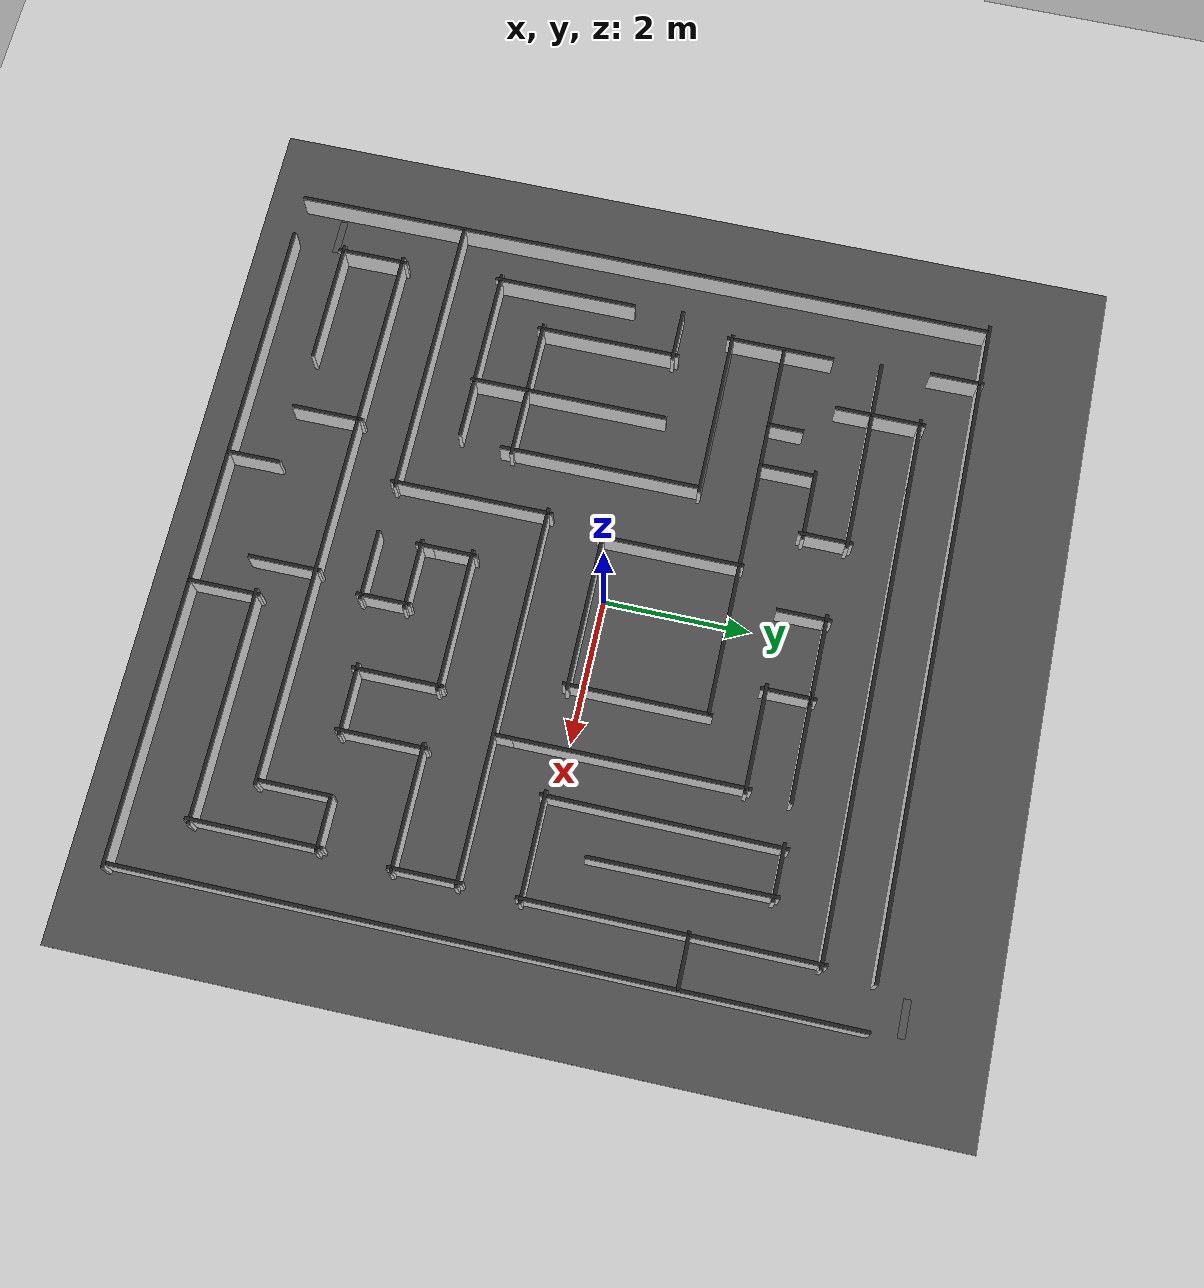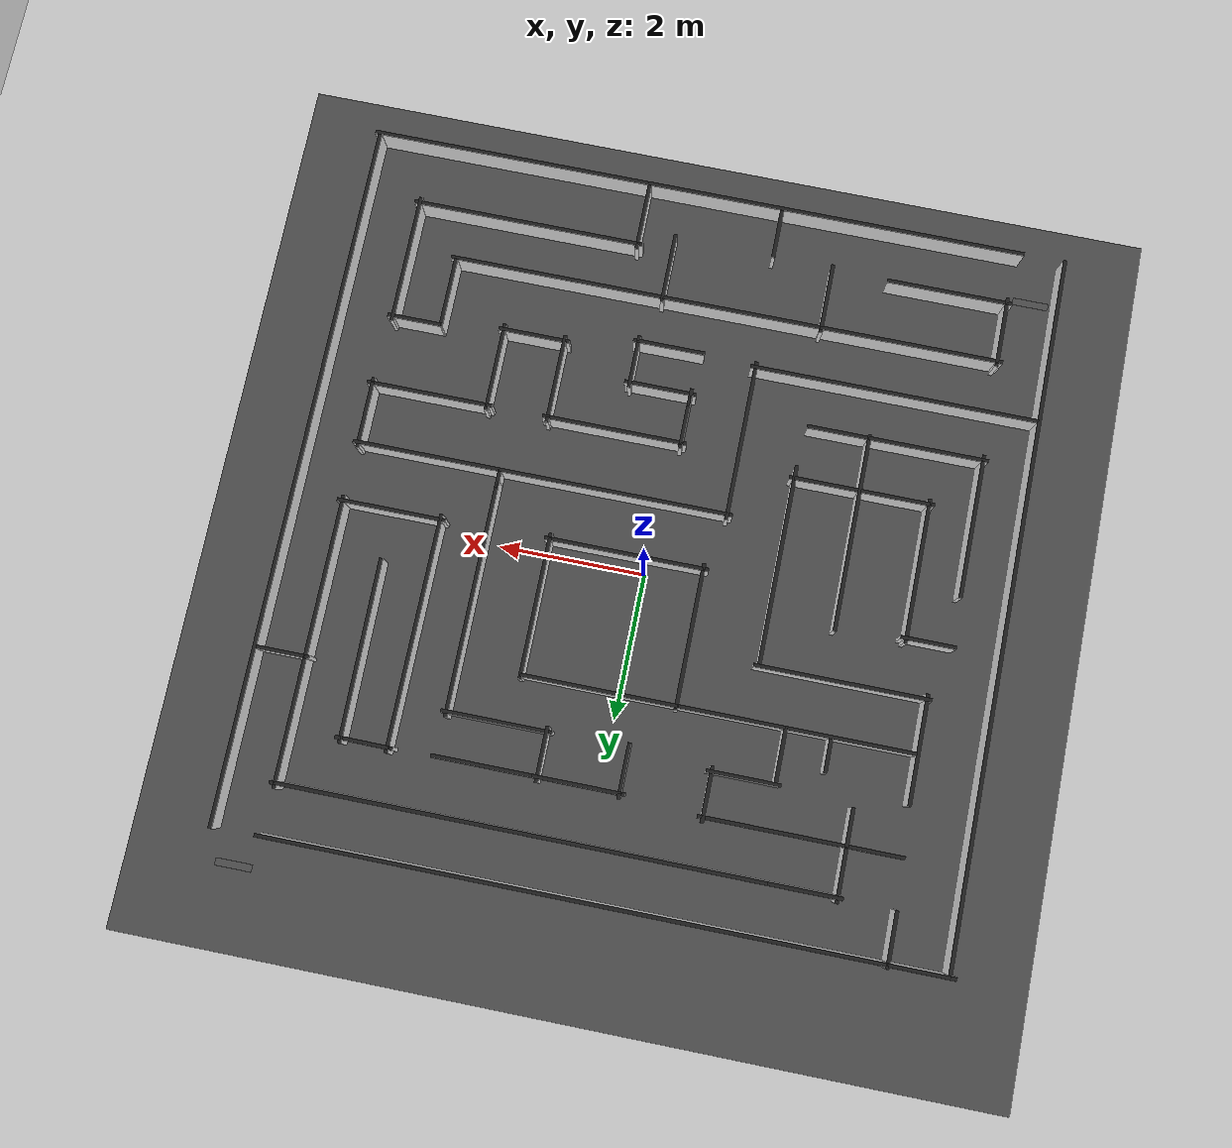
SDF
<sdf version="1.6">
 <world name="default">
  <light name="sun" type="directional">
   <pose>0 0 10 0 -0 0</pose>
   <diffuse>0.8 0.8 0.8 1</diffuse>
   <specular>0.1 0.1 0.1 1</specular>
   <attenuation>
    <range>1000</range>
    <constant>0.9</constant>
    <linear>0.01</linear>
    <quadratic>0.001</quadratic>
   </attenuation>
   <direction>-0.5 0.5 -1</direction>
  </light>
  <model name="ground_plane">
   <static>1</static>
   <link name="link">
    <collision name="collision">
     <geometry><plane><normal>0 0 1</normal><size>100 100</size></plane></geometry>
     <surface><friction><ode><mu>100</mu><mu2>50</mu2></ode></friction></surface>
    </collision>
    <visual name="visual">
     <cast_shadows>0</cast_shadows>
     <geometry><plane><normal>0 0 1</normal><size>100 100</size></plane></geometry>
     <material>
      <script><uri>file://media/materials/scripts/gazebo.material</uri><name>Gazebo/Grey</name></script>
     </material>
    </visual>
   </link>
  </model>
  <gravity>0 0 -9.8</gravity>
  <magnetic_field>6e-06 2.3e-05 -4.2e-05</magnetic_field>
  <atmosphere type="adiabatic"/>
  <physics name="default_physics" default="0" type="ode">
   <max_step_size>0.001</max_step_size>
   <real_time_factor>1</real_time_factor>
   <real_time_update_rate>1000</real_time_update_rate>
  </physics>
  <scene><ambient>0.4 0.4 0.4 1</ambient><background>0.7 0.7 0.7 1</background><shadows>1</shadows></scene>
  <spherical_coordinates>
   <surface_model>EARTH_WGS84</surface_model>
   <latitude_deg>0</latitude_deg>
   <longitude_deg>0</longitude_deg>
   <elevation>0</elevation>
   <heading_deg>0</heading_deg>
  </spherical_coordinates>
  <model name="10x10_maze_1_body_0">
   <pose>0 -0.5 0 0 -0 0</pose>
   <link name="Wall_0">
    <collision name="Wall_0_Collision">
     <geometry><box><size>9.83 0.05 0.4</size></box></geometry>
     <pose>0 0 0.2 0 -0 0</pose>
    </collision>
    <visual name="Wall_0_Visual">
     <pose>0 0 0.2 0 -0 0</pose>
     <geometry><box><size>9.83 0.05 0.4</size></box></geometry>
     <material>
      <script><uri>file://media/materials/scripts/gazebo.material</uri><name>Gazebo/White</name></script>
      <ambient>1 1 1 1</ambient>
     </material>
    </visual>
    <pose>-4.87625 -0.01472 0 0 0 -1.5708</pose>
   </link>
   <link name="Wall_103">
    <collision name="Wall_103_Collision">
     <geometry><box><size>0.5 0.05 0.4</size></box></geometry>
     <pose>0 0 0.2 0 -0 0</pose>
    </collision>
    <visual name="Wall_103_Visual">
     <pose>0 0 0.2 0 -0 0</pose>
     <geometry><box><size>0.5 0.05 0.4</size></box></geometry>
     <material>
      <script><uri>file://media/materials/scripts/gazebo.material</uri><name>Gazebo/White</name></script>
      <ambient>1 1 1 1</ambient>
     </material>
    </visual>
    <pose>-2.85325 2.41853 0 0 -0 1.5708</pose>
   </link>
   <link name="Wall_106">
    <collision name="Wall_106_Collision">
     <geometry><box><size>6.77039 0.05 0.4</size></box></geometry>
     <pose>0 0 0.2 0 -0 0</pose>
    </collision>
    <visual name="Wall_106_Visual">
     <pose>0 0 0.2 0 -0 0</pose>
     <geometry><box><size>6.77039 0.05 0.4</size></box></geometry>
     <material>
      <script><uri>file://media/materials/scripts/gazebo.material</uri><name>Gazebo/White</name></script>
      <ambient>1 1 1 1</ambient>
     </material>
    </visual>
    <pose>0.865745 4.20453 0 0 -0 0</pose>
   </link>
   <link name="Wall_107">
    <collision name="Wall_107_Collision">
     <geometry><box><size>4 0.05 0.4</size></box></geometry>
     <pose>0 0 0.2 0 -0 0</pose>
    </collision>
    <visual name="Wall_107_Visual">
     <pose>0 0 0.2 0 -0 0</pose>
     <geometry><box><size>4 0.05 0.4</size></box></geometry>
     <material>
      <script><uri>file://media/materials/scripts/gazebo.material</uri><name>Gazebo/White</name></script>
      <ambient>1 1 1 1</ambient>
     </material>
    </visual>
    <pose>4.17575 2.27953 0 0 0 -1.5708</pose>
   </link>
   <link name="Wall_108">
    <collision name="Wall_108_Collision">
     <geometry><box><size>1.5 0.05 0.4</size></box></geometry>
     <pose>0 0 0.2 0 -0 0</pose>
    </collision>
    <visual name="Wall_108_Visual">
     <pose>0 0 0.2 0 -0 0</pose>
     <geometry><box><size>1.5 0.05 0.4</size></box></geometry>
     <material>
      <script><uri>file://media/materials/scripts/gazebo.material</uri><name>Gazebo/White</name></script>
      <ambient>1 1 1 1</ambient>
     </material>
    </visual>
    <pose>3.50075 0.354528 0 0 -0 3.14159</pose>
   </link>
   <link name="Wall_109">
    <collision name="Wall_109_Collision">
     <geometry><box><size>3.26525 0.05 0.4</size></box></geometry>
     <pose>0 0 0.2 0 -0 0</pose>
    </collision>
    <visual name="Wall_109_Visual">
     <pose>0 0 0.2 0 -0 0</pose>
     <geometry><box><size>3.26525 0.05 0.4</size></box></geometry>
     <material>
      <script><uri>file://media/materials/scripts/gazebo.material</uri><name>Gazebo/White</name></script>
      <ambient>1 1 1 1</ambient>
     </material>
    </visual>
    <pose>2.83324 1.91203 0 0 -0 1.56598</pose>
   </link>
   <link name="Wall_110">
    <collision name="Wall_110_Collision">
     <geometry><box><size>0.779601 0.05 0.4</size></box></geometry>
     <pose>0 0 0.2 0 -0 0</pose>
    </collision>
    <visual name="Wall_110_Visual">
     <pose>0 0 0.2 0 -0 0</pose>
     <geometry><box><size>0.779601 0.05 0.4</size></box></geometry>
     <material>
      <script><uri>file://media/materials/scripts/gazebo.material</uri><name>Gazebo/White</name></script>
      <ambient>1 1 1 1</ambient>
     </material>
    </visual>
    <pose>3.15575 3.46703 0 0 0 -0.007936</pose>
   </link>
   <link name="Wall_111">
    <collision name="Wall_111_Collision">
     <geometry><box><size>2.51521 0.05 0.4</size></box></geometry>
     <pose>0 0 0.2 0 -0 0</pose>
    </collision>
    <visual name="Wall_111_Visual">
     <pose>0 0 0.2 0 -0 0</pose>
     <geometry><box><size>2.51521 0.05 0.4</size></box></geometry>
     <material>
      <script><uri>file://media/materials/scripts/gazebo.material</uri><name>Gazebo/White</name></script>
      <ambient>1 1 1 1</ambient>
     </material>
    </visual>
    <pose>3.47824 2.28213 0 0 0 -1.56445</pose>
   </link>
   <link name="Wall_113">
    <collision name="Wall_113_Collision">
     <geometry><box><size>1.5 0.05 0.4</size></box></geometry>
     <pose>0 0 0.2 0 -0 0</pose>
    </collision>
    <visual name="Wall_113_Visual">
     <pose>0 0 0.2 0 -0 0</pose>
     <geometry><box><size>1.5 0.05 0.4</size></box></geometry>
     <material>
      <script><uri>file://media/materials/scripts/gazebo.material</uri><name>Gazebo/White</name></script>
      <ambient>1 1 1 1</ambient>
     </material>
    </visual>
    <pose>1.50675 2.85353 0 0 -0 3.14159</pose>
   </link>
   <link name="Wall_114">
    <collision name="Wall_114_Collision">
     <geometry><box><size>0.75 0.05 0.4</size></box></geometry>
     <pose>0 0 0.2 0 -0 0</pose>
    </collision>
    <visual name="Wall_114_Visual">
     <pose>0 0 0.2 0 -0 0</pose>
     <geometry><box><size>0.75 0.05 0.4</size></box></geometry>
     <material>
      <script><uri>file://media/materials/scripts/gazebo.material</uri><name>Gazebo/White</name></script>
      <ambient>1 1 1 1</ambient>
     </material>
    </visual>
    <pose>0.831745 3.15353 0 0 -0 1.5708</pose>
   </link>
   <link name="Wall_115">
    <collision name="Wall_115_Collision">
     <geometry><box><size>1.25 0.05 0.4</size></box></geometry>
     <pose>0 0 0.2 0 -0 0</pose>
    </collision>
    <visual name="Wall_115_Visual">
     <pose>0 0 0.2 0 -0 0</pose>
     <geometry><box><size>1.25 0.05 0.4</size></box></geometry>
     <material>
      <script><uri>file://media/materials/scripts/gazebo.material</uri><name>Gazebo/White</name></script>
      <ambient>1 1 1 1</ambient>
     </material>
    </visual>
    <pose>0.281745 3.45353 0 0 -0 3.14159</pose>
   </link>
   <link name="Wall_116">
    <collision name="Wall_116_Collision">
     <geometry><box><size>0.75 0.05 0.4</size></box></geometry>
     <pose>0 0 0.2 0 -0 0</pose>
    </collision>
    <visual name="Wall_116_Visual">
     <pose>0 0 0.2 0 -0 0</pose>
     <geometry><box><size>0.75 0.05 0.4</size></box></geometry>
     <material>
      <script><uri>file://media/materials/scripts/gazebo.material</uri><name>Gazebo/White</name></script>
      <ambient>1 1 1 1</ambient>
     </material>
    </visual>
    <pose>-0.268255 3.15353 0 0 0 -1.5708</pose>
   </link>
   <link name="Wall_118">
    <collision name="Wall_118_Collision">
     <geometry><box><size>1.5 0.05 0.4</size></box></geometry>
     <pose>0 0 0.2 0 -0 0</pose>
    </collision>
    <visual name="Wall_118_Visual">
     <pose>0 0 0.2 0 -0 0</pose>
     <geometry><box><size>1.5 0.05 0.4</size></box></geometry>
     <material>
      <script><uri>file://media/materials/scripts/gazebo.material</uri><name>Gazebo/White</name></script>
      <ambient>1 1 1 1</ambient>
     </material>
    </visual>
    <pose>1.50675 3.45353 0 0 -0 0</pose>
   </link>
   <link name="Wall_122">
    <collision name="Wall_122_Collision">
     <geometry><box><size>1 0.05 0.4</size></box></geometry>
     <pose>0 0 0.2 0 -0 0</pose>
    </collision>
    <visual name="Wall_122_Visual">
     <pose>0 0 0.2 0 -0 0</pose>
     <geometry><box><size>1 0.05 0.4</size></box></geometry>
     <material>
      <script><uri>file://media/materials/scripts/gazebo.material</uri><name>Gazebo/White</name></script>
      <ambient>1 1 1 1</ambient>
     </material>
    </visual>
    <pose>-2.86925 4.20453 0 0 -0 3.14159</pose>
   </link>
   <link name="Wall_123">
    <collision name="Wall_123_Collision">
     <geometry><box><size>1.25 0.05 0.4</size></box></geometry>
     <pose>0 0 0.2 0 -0 0</pose>
    </collision>
    <visual name="Wall_123_Visual">
     <pose>0 0 0.2 0 -0 0</pose>
     <geometry><box><size>1.25 0.05 0.4</size></box></geometry>
     <material>
      <script><uri>file://media/materials/scripts/gazebo.material</uri><name>Gazebo/White</name></script>
      <ambient>1 1 1 1</ambient>
     </material>
    </visual>
    <pose>-3.29426 3.65453 0 0 0 -1.5708</pose>
   </link>
   <link name="Wall_125">
    <collision name="Wall_125_Collision">
     <geometry><box><size>0.75 0.05 0.4</size></box></geometry>
     <pose>0 0 0.2 0 -0 0</pose>
    </collision>
    <visual name="Wall_125_Visual">
     <pose>0 0 0.2 0 -0 0</pose>
     <geometry><box><size>0.75 0.05 0.4</size></box></geometry>
     <material>
      <script><uri>file://media/materials/scripts/gazebo.material</uri><name>Gazebo/White</name></script>
      <ambient>1 1 1 1</ambient>
     </material>
    </visual>
    <pose>4.49375 2.51153 0 0 -0 0</pose>
   </link>
   <link name="Wall_134">
    <collision name="Wall_134_Collision">
     <geometry><box><size>0.75 0.05 0.4</size></box></geometry>
     <pose>0 0 0.2 0 -0 0</pose>
    </collision>
    <visual name="Wall_134_Visual">
     <pose>0 0 0.2 0 -0 0</pose>
     <geometry><box><size>0.75 0.05 0.4</size></box></geometry>
     <material>
      <script><uri>file://media/materials/scripts/gazebo.material</uri><name>Gazebo/White</name></script>
      <ambient>1 1 1 1</ambient>
     </material>
    </visual>
    <pose>-3.89825 0.701528 0 0 -0 3.14159</pose>
   </link>
   <link name="Wall_136">
    <collision name="Wall_136_Collision">
     <geometry><box><size>5.32 0.05 0.4</size></box></geometry>
     <pose>0 0 0.2 0 -0 0</pose>
    </collision>
    <visual name="Wall_136_Visual">
     <pose>0 0 0.2 0 -0 0</pose>
     <geometry><box><size>5.32 0.05 0.4</size></box></geometry>
     <material>
      <script><uri>file://media/materials/scripts/gazebo.material</uri><name>Gazebo/White</name></script>
      <ambient>1 1 1 1</ambient>
     </material>
    </visual>
    <pose>-1.33126 2.18653 0 0 -0 3.14159</pose>
   </link>
   <link name="Wall_139">
    <collision name="Wall_139_Collision">
     <geometry><box><size>2.25 0.05 0.4</size></box></geometry>
     <pose>0 0 0.2 0 -0 0</pose>
    </collision>
    <visual name="Wall_139_Visual">
     <pose>0 0 0.2 0 -0 0</pose>
     <geometry><box><size>2.25 0.05 0.4</size></box></geometry>
     <material>
      <script><uri>file://media/materials/scripts/gazebo.material</uri><name>Gazebo/White</name></script>
      <ambient>1 1 1 1</ambient>
     </material>
    </visual>
    <pose>0.274745 0.319528 0 0 -0 0</pose>
   </link>
   <link name="Wall_14">
    <collision name="Wall_14_Collision">
     <geometry><box><size>7.75 0.05 0.4</size></box></geometry>
     <pose>0 0 0.2 0 -0 0</pose>
    </collision>
    <visual name="Wall_14_Visual">
     <pose>0 0 0.2 0 -0 0</pose>
     <geometry><box><size>7.75 0.05 0.4</size></box></geometry>
     <material>
      <script><uri>file://media/materials/scripts/gazebo.material</uri><name>Gazebo/White</name></script>
      <ambient>1 1 1 1</ambient>
     </material>
    </visual>
    <pose>-0.382255 -3.30847 0 0 -0 3.14159</pose>
   </link>
   <link name="Wall_140">
    <collision name="Wall_140_Collision">
     <geometry><box><size>2 0.05 0.4</size></box></geometry>
     <pose>0 0 0.2 0 -0 0</pose>
    </collision>
    <visual name="Wall_140_Visual">
     <pose>0 0 0.2 0 -0 0</pose>
     <geometry><box><size>2 0.05 0.4</size></box></geometry>
     <material>
      <script><uri>file://media/materials/scripts/gazebo.material</uri><name>Gazebo/White</name></script>
      <ambient>1 1 1 1</ambient>
     </material>
    </visual>
    <pose>1.32475 1.24453 0 0 -0 1.5708</pose>
   </link>
   <link name="Wall_143">
    <collision name="Wall_143_Collision">
     <geometry><box><size>1 0.05 0.4</size></box></geometry>
     <pose>0 0 0.2 0 -0 0</pose>
    </collision>
    <visual name="Wall_143_Visual">
     <pose>0 0 0.2 0 -0 0</pose>
     <geometry><box><size>1 0.05 0.4</size></box></geometry>
     <material>
      <script><uri>file://media/materials/scripts/gazebo.material</uri><name>Gazebo/White</name></script>
      <ambient>1 1 1 1</ambient>
     </material>
    </visual>
    <pose>-4.18225 -3.73347 0 0 0 -1.5708</pose>
   </link>
   <link name="Wall_144">
    <collision name="Wall_144_Collision">
     <geometry><box><size>1.75 0.05 0.4</size></box></geometry>
     <pose>0 0 0.2 0 -0 0</pose>
    </collision>
    <visual name="Wall_144_Visual">
     <pose>0 0 0.2 0 -0 0</pose>
     <geometry><box><size>1.75 0.05 0.4</size></box></geometry>
     <material>
      <script><uri>file://media/materials/scripts/gazebo.material</uri><name>Gazebo/White</name></script>
      <ambient>1 1 1 1</ambient>
     </material>
    </visual>
    <pose>-3.38225 -4.15847 0 0 -0 0</pose>
   </link>
   <link name="Wall_146">
    <collision name="Wall_146_Collision">
     <geometry><box><size>1 0.05 0.4</size></box></geometry>
     <pose>0 0 0.2 0 -0 0</pose>
    </collision>
    <visual name="Wall_146_Visual">
     <pose>0 0 0.2 0 -0 0</pose>
     <geometry><box><size>1 0.05 0.4</size></box></geometry>
     <material>
      <script><uri>file://media/materials/scripts/gazebo.material</uri><name>Gazebo/White</name></script>
      <ambient>1 1 1 1</ambient>
     </material>
    </visual>
    <pose>-1.73026 -3.73547 0 0 0 -1.5708</pose>
   </link>
   <link name="Wall_149">
    <collision name="Wall_149_Collision">
     <geometry><box><size>0.75 0.05 0.4</size></box></geometry>
     <pose>0 0 0.2 0 -0 0</pose>
    </collision>
    <visual name="Wall_149_Visual">
     <pose>0 0 0.2 0 -0 0</pose>
     <geometry><box><size>0.75 0.05 0.4</size></box></geometry>
     <material>
      <script><uri>file://media/materials/scripts/gazebo.material</uri><name>Gazebo/White</name></script>
      <ambient>1 1 1 1</ambient>
     </material>
    </visual>
    <pose>-0.892255 -4.55247 0 0 -0 1.5708</pose>
   </link>
   <link name="Wall_151">
    <collision name="Wall_151_Collision">
     <geometry><box><size>1 0.05 0.4</size></box></geometry>
     <pose>0 0 0.2 0 -0 0</pose>
    </collision>
    <visual name="Wall_151_Visual">
     <pose>0 0 0.2 0 -0 0</pose>
     <geometry><box><size>1 0.05 0.4</size></box></geometry>
     <material>
      <script><uri>file://media/materials/scripts/gazebo.material</uri><name>Gazebo/White</name></script>
      <ambient>1 1 1 1</ambient>
     </material>
    </visual>
    <pose>0.49745 -3.7387 0 0 0 -1.5708</pose>
   </link>
   <link name="Wall_153">
    <collision name="Wall_153_Collision">
     <geometry><box><size>1 0.05 0.4</size></box></geometry>
     <pose>0 0 0.2 0 -0 0</pose>
    </collision>
    <visual name="Wall_153_Visual">
     <pose>0 0 0.2 0 -0 0</pose>
     <geometry><box><size>1 0.05 0.4</size></box></geometry>
     <material>
      <script><uri>file://media/materials/scripts/gazebo.material</uri><name>Gazebo/White</name></script>
      <ambient>1 1 1 1</ambient>
     </material>
    </visual>
    <pose>0.993745 -4.42747 0 0 -0 1.5708</pose>
   </link>
   <link name="Wall_154">
    <collision name="Wall_154_Collision">
     <geometry><box><size>3.25 0.05 0.4</size></box></geometry>
     <pose>0 0 0.2 0 -0 0</pose>
    </collision>
    <visual name="Wall_154_Visual">
     <pose>0 0 0.2 0 -0 0</pose>
     <geometry><box><size>3.25 0.05 0.4</size></box></geometry>
     <material>
      <script><uri>file://media/materials/scripts/gazebo.material</uri><name>Gazebo/White</name></script>
      <ambient>1 1 1 1</ambient>
     </material>
    </visual>
    <pose>2.54374 -4.00247 0 0 -0 0</pose>
   </link>
   <link name="Wall_155">
    <collision name="Wall_155_Collision">
     <geometry><box><size>1.83502 0.05 0.4</size></box></geometry>
     <pose>0 0 0.2 0 -0 0</pose>
    </collision>
    <visual name="Wall_155_Visual">
     <pose>0 0 0.2 0 -0 0</pose>
     <geometry><box><size>1.83502 0.05 0.4</size></box></geometry>
     <material>
      <script><uri>file://media/materials/scripts/gazebo.material</uri><name>Gazebo/White</name></script>
      <ambient>1 1 1 1</ambient>
     </material>
    </visual>
    <pose>4.09489 -3.15997 0 0 -0 1.56944</pose>
   </link>
   <link name="Wall_16">
    <collision name="Wall_16_Collision">
     <geometry><box><size>4 0.05 0.4</size></box></geometry>
     <pose>0 0 0.2 0 -0 0</pose>
    </collision>
    <visual name="Wall_16_Visual">
     <pose>0 0 0.2 0 -0 0</pose>
     <geometry><box><size>4 0.05 0.4</size></box></geometry>
     <material>
      <script><uri>file://media/materials/scripts/gazebo.material</uri><name>Gazebo/White</name></script>
      <ambient>1 1 1 1</ambient>
     </material>
    </visual>
    <pose>-2.87325 -2.57647 0 0 -0 0</pose>
   </link>
   <link name="Wall_168">
    <collision name="Wall_168_Collision">
     <geometry><box><size>2.3965 0.05 0.4</size></box></geometry>
     <pose>0 0 0.2 0 -0 0</pose>
    </collision>
    <visual name="Wall_168_Visual">
     <pose>0 0 0.2 0 -0 0</pose>
     <geometry><box><size>2.3965 0.05 0.4</size></box></geometry>
     <material>
      <script><uri>file://media/materials/scripts/gazebo.material</uri><name>Gazebo/White</name></script>
      <ambient>1 1 1 1</ambient>
     </material>
    </visual>
    <pose>-2.8715 1.45153 0 0 -0 3.14159</pose>
   </link>
   <link name="Wall_169">
    <collision name="Wall_169_Collision">
     <geometry><box><size>1.5 0.05 0.4</size></box></geometry>
     <pose>0 0 0.2 0 -0 0</pose>
    </collision>
    <visual name="Wall_169_Visual">
     <pose>0 0 0.2 0 -0 0</pose>
     <geometry><box><size>1.5 0.05 0.4</size></box></geometry>
     <material>
      <script><uri>file://media/materials/scripts/gazebo.material</uri><name>Gazebo/White</name></script>
      <ambient>1 1 1 1</ambient>
     </material>
    </visual>
    <pose>-4.00626 2.12653 0 0 -0 1.5708</pose>
   </link>
   <link name="Wall_173">
    <collision name="Wall_173_Collision">
     <geometry><box><size>0.75 0.05 0.4</size></box></geometry>
     <pose>0 0 0.2 0 -0 0</pose>
    </collision>
    <visual name="Wall_173_Visual">
     <pose>0 0 0.2 0 -0 0</pose>
     <geometry><box><size>0.75 0.05 0.4</size></box></geometry>
     <material>
      <script><uri>file://media/materials/scripts/gazebo.material</uri><name>Gazebo/White</name></script>
      <ambient>1 1 1 1</ambient>
     </material>
    </visual>
    <pose>3.79388 -2.31747 0 0 -0 3.14159</pose>
   </link>
   <link name="Wall_175">
    <collision name="Wall_175_Collision">
     <geometry><box><size>1 0.05 0.4</size></box></geometry>
     <pose>0 0 0.2 0 -0 0</pose>
    </collision>
    <visual name="Wall_175_Visual">
     <pose>0 0 0.2 0 -0 0</pose>
     <geometry><box><size>1 0.05 0.4</size></box></geometry>
     <material>
      <script><uri>file://media/materials/scripts/gazebo.material</uri><name>Gazebo/White</name></script>
      <ambient>1 1 1 1</ambient>
     </material>
    </visual>
    <pose>3.41775 -2.79347 0 0 -0 1.5708</pose>
   </link>
   <link name="Wall_3">
    <collision name="Wall_3_Collision">
     <geometry><box><size>9.25 0.05 0.4</size></box></geometry>
     <pose>0 0 0.2 0 -0 0</pose>
    </collision>
    <visual name="Wall_3_Visual">
     <pose>0 0 0.2 0 -0 0</pose>
     <geometry><box><size>9.25 0.05 0.4</size></box></geometry>
     <material>
      <script><uri>file://media/materials/scripts/gazebo.material</uri><name>Gazebo/White</name></script>
      <ambient>1 1 1 1</ambient>
     </material>
    </visual>
    <pose>0.317745 -4.90847 0 0 -0 0</pose>
   </link>
   <link name="Wall_32">
    <collision name="Wall_32_Collision">
     <geometry><box><size>2.25 0.05 0.4</size></box></geometry>
     <pose>0 0 0.2 0 -0 0</pose>
    </collision>
    <visual name="Wall_32_Visual">
     <pose>0 0 0.2 0 -0 0</pose>
     <geometry><box><size>2.25 0.05 0.4</size></box></geometry>
     <material>
      <script><uri>file://media/materials/scripts/gazebo.material</uri><name>Gazebo/White</name></script>
      <ambient>1 1 1 1</ambient>
     </material>
    </visual>
    <pose>-0.948255 -1.52647 0 0 -0 1.5708</pose>
   </link>
   <link name="Wall_33">
    <collision name="Wall_33_Collision">
     <geometry><box><size>5.25 0.05 0.4</size></box></geometry>
     <pose>0 0 0.2 0 -0 0</pose>
    </collision>
    <visual name="Wall_33_Visual">
     <pose>0 0 0.2 0 -0 0</pose>
     <geometry><box><size>5.25 0.05 0.4</size></box></geometry>
     <material>
      <script><uri>file://media/materials/scripts/gazebo.material</uri><name>Gazebo/White</name></script>
      <ambient>1 1 1 1</ambient>
     </material>
    </visual>
    <pose>1.60174 -0.476472 0 0 -0 0</pose>
   </link>
   <link name="Wall_34">
    <collision name="Wall_34_Collision">
     <geometry><box><size>1 0.05 0.4</size></box></geometry>
     <pose>0 0 0.2 0 -0 0</pose>
    </collision>
    <visual name="Wall_34_Visual">
     <pose>0 0 0.2 0 -0 0</pose>
     <geometry><box><size>1 0.05 0.4</size></box></geometry>
     <material>
      <script><uri>file://media/materials/scripts/gazebo.material</uri><name>Gazebo/White</name></script>
      <ambient>1 1 1 1</ambient>
     </material>
    </visual>
    <pose>4.15175 -0.901472 0 0 0 -1.5708</pose>
   </link>
   <link name="Wall_35">
    <collision name="Wall_35_Collision">
     <geometry><box><size>1.75 0.05 0.4</size></box></geometry>
     <pose>0 0 0.2 0 -0 0</pose>
    </collision>
    <visual name="Wall_35_Visual">
     <pose>0 0 0.2 0 -0 0</pose>
     <geometry><box><size>1.75 0.05 0.4</size></box></geometry>
     <material>
      <script><uri>file://media/materials/scripts/gazebo.material</uri><name>Gazebo/White</name></script>
      <ambient>1 1 1 1</ambient>
     </material>
    </visual>
    <pose>3.35175 -1.32647 0 0 -0 3.14159</pose>
   </link>
   <link name="Wall_36">
    <collision name="Wall_36_Collision">
     <geometry><box><size>1.25 0.05 0.4</size></box></geometry>
     <pose>0 0 0.2 0 -0 0</pose>
    </collision>
    <visual name="Wall_36_Visual">
     <pose>0 0 0.2 0 -0 0</pose>
     <geometry><box><size>1.25 0.05 0.4</size></box></geometry>
     <material>
      <script><uri>file://media/materials/scripts/gazebo.material</uri><name>Gazebo/White</name></script>
      <ambient>1 1 1 1</ambient>
     </material>
    </visual>
    <pose>2.55174 -1.87647 0 0 0 -1.5708</pose>
   </link>
   <link name="Wall_37">
    <collision name="Wall_37_Collision">
     <geometry><box><size>1 0.05 0.4</size></box></geometry>
     <pose>0 0 0.2 0 -0 0</pose>
    </collision>
    <visual name="Wall_37_Visual">
     <pose>0 0 0.2 0 -0 0</pose>
     <geometry><box><size>1 0.05 0.4</size></box></geometry>
     <material>
      <script><uri>file://media/materials/scripts/gazebo.material</uri><name>Gazebo/White</name></script>
      <ambient>1 1 1 1</ambient>
     </material>
    </visual>
    <pose>2.12675 -2.42647 0 0 -0 3.14159</pose>
   </link>
   <link name="Wall_38">
    <collision name="Wall_38_Collision">
     <geometry><box><size>1.25 0.05 0.4</size></box></geometry>
     <pose>0 0 0.2 0 -0 0</pose>
    </collision>
    <visual name="Wall_38_Visual">
     <pose>0 0 0.2 0 -0 0</pose>
     <geometry><box><size>1.25 0.05 0.4</size></box></geometry>
     <material>
      <script><uri>file://media/materials/scripts/gazebo.material</uri><name>Gazebo/White</name></script>
      <ambient>1 1 1 1</ambient>
     </material>
    </visual>
    <pose>1.70175 -1.87647 0 0 -0 1.5708</pose>
   </link>
   <link name="Wall_39">
    <collision name="Wall_39_Collision">
     <geometry><box><size>2 0.05 0.4</size></box></geometry>
     <pose>0 0 0.2 0 -0 0</pose>
    </collision>
    <visual name="Wall_39_Visual">
     <pose>0 0 0.2 0 -0 0</pose>
     <geometry><box><size>2 0.05 0.4</size></box></geometry>
     <material>
      <script><uri>file://media/materials/scripts/gazebo.material</uri><name>Gazebo/White</name></script>
      <ambient>1 1 1 1</ambient>
     </material>
    </visual>
    <pose>0.776745 -1.32647 0 0 -0 3.14159</pose>
   </link>
   <link name="Wall_4">
    <collision name="Wall_4_Collision">
     <geometry><box><size>9.83 0.05 0.4</size></box></geometry>
     <pose>0 0 0.2 0 -0 0</pose>
    </collision>
    <visual name="Wall_4_Visual">
     <pose>0 0 0.2 0 -0 0</pose>
     <geometry><box><size>9.83 0.05 0.4</size></box></geometry>
     <material>
      <script><uri>file://media/materials/scripts/gazebo.material</uri><name>Gazebo/White</name></script>
      <ambient>1 1 1 1</ambient>
     </material>
    </visual>
    <pose>4.86775 0.02628 0 0 -0 1.5708</pose>
   </link>
   <link name="Wall_40">
    <collision name="Wall_40_Collision">
     <geometry><box><size>0.75 0.05 0.4</size></box></geometry>
     <pose>0 0 0.2 0 -0 0</pose>
    </collision>
    <visual name="Wall_40_Visual">
     <pose>0 0 0.2 0 -0 0</pose>
     <geometry><box><size>0.75 0.05 0.4</size></box></geometry>
     <material>
      <script><uri>file://media/materials/scripts/gazebo.material</uri><name>Gazebo/White</name></script>
      <ambient>1 1 1 1</ambient>
     </material>
    </visual>
    <pose>-0.148255 -1.62647 0 0 0 -1.5708</pose>
   </link>
   <link name="Wall_41">
    <collision name="Wall_41_Collision">
     <geometry><box><size>0.25 0.05 0.4</size></box></geometry>
     <pose>0 0 0.2 0 -0 0</pose>
    </collision>
    <visual name="Wall_41_Visual">
     <pose>0 0 0.2 0 -0 0</pose>
     <geometry><box><size>0.25 0.05 0.4</size></box></geometry>
     <material>
      <script><uri>file://media/materials/scripts/gazebo.material</uri><name>Gazebo/White</name></script>
      <ambient>1 1 1 1</ambient>
     </material>
    </visual>
    <pose>-0.148255 -1.97647 0 0 0 -1.5708</pose>
   </link>
   <link name="Wall_42">
    <collision name="Wall_42_Collision">
     <geometry><box><size>1 0.05 0.4</size></box></geometry>
     <pose>0 0 0.2 0 -0 0</pose>
    </collision>
    <visual name="Wall_42_Visual">
     <pose>0 0 0.2 0 -0 0</pose>
     <geometry><box><size>1 0.05 0.4</size></box></geometry>
     <material>
      <script><uri>file://media/materials/scripts/gazebo.material</uri><name>Gazebo/White</name></script>
      <ambient>1 1 1 1</ambient>
     </material>
    </visual>
    <pose>0.276745 -2.02647 0 0 -0 0</pose>
   </link>
   <link name="Wall_43">
    <collision name="Wall_43_Collision">
     <geometry><box><size>0.75 0.05 0.4</size></box></geometry>
     <pose>0 0 0.2 0 -0 0</pose>
    </collision>
    <visual name="Wall_43_Visual">
     <pose>0 0 0.2 0 -0 0</pose>
     <geometry><box><size>0.75 0.05 0.4</size></box></geometry>
     <material>
      <script><uri>file://media/materials/scripts/gazebo.material</uri><name>Gazebo/White</name></script>
      <ambient>1 1 1 1</ambient>
     </material>
    </visual>
    <pose>0.701745 -2.32647 0 0 0 -1.5708</pose>
   </link>
   <link name="Wall_44">
    <collision name="Wall_44_Collision">
     <geometry><box><size>1 0.05 0.4</size></box></geometry>
     <pose>0 0 0.2 0 -0 0</pose>
    </collision>
    <visual name="Wall_44_Visual">
     <pose>0 0 0.2 0 -0 0</pose>
     <geometry><box><size>1 0.05 0.4</size></box></geometry>
     <material>
      <script><uri>file://media/materials/scripts/gazebo.material</uri><name>Gazebo/White</name></script>
      <ambient>1 1 1 1</ambient>
     </material>
    </visual>
    <pose>0.276745 -2.62647 0 0 -0 3.14159</pose>
   </link>
   <link name="Wall_46">
    <collision name="Wall_46_Collision">
     <geometry><box><size>2 0.05 0.4</size></box></geometry>
     <pose>0 0 0.2 0 -0 0</pose>
    </collision>
    <visual name="Wall_46_Visual">
     <pose>0 0 0.2 0 -0 0</pose>
     <geometry><box><size>2 0.05 0.4</size></box></geometry>
     <material>
      <script><uri>file://media/materials/scripts/gazebo.material</uri><name>Gazebo/White</name></script>
      <ambient>1 1 1 1</ambient>
     </material>
    </visual>
    <pose>-4.21425 -0.968472 0 0 -0 1.5708</pose>
   </link>
   <link name="Wall_6">
    <collision name="Wall_6_Collision">
     <geometry><box><size>9.25 0.05 0.4</size></box></geometry>
     <pose>0 0 0.2 0 -0 0</pose>
    </collision>
    <visual name="Wall_6_Visual">
     <pose>0 0 0.2 0 -0 0</pose>
     <geometry><box><size>9.25 0.05 0.4</size></box></geometry>
     <material>
      <script><uri>file://media/materials/scripts/gazebo.material</uri><name>Gazebo/White</name></script>
      <ambient>1 1 1 1</ambient>
     </material>
    </visual>
    <pose>-0.343745 4.90753 0 0 -0 0</pose>
   </link>
   <link name="Wall_63">
    <collision name="Wall_63_Collision">
     <geometry><box><size>2.5 0.05 0.4</size></box></geometry>
     <pose>0 0 0.2 0 -0 0</pose>
    </collision>
    <visual name="Wall_63_Visual">
     <pose>0 0 0.2 0 -0 0</pose>
     <geometry><box><size>2.5 0.05 0.4</size></box></geometry>
     <material>
      <script><uri>file://media/materials/scripts/gazebo.material</uri><name>Gazebo/White</name></script>
      <ambient>1 1 1 1</ambient>
     </material>
    </visual>
    <pose>-3.03925 -1.89347 0 0 -0 0</pose>
   </link>
   <link name="Wall_77">
    <collision name="Wall_77_Collision">
     <geometry><box><size>2 0.05 0.4</size></box></geometry>
     <pose>0 0 0.2 0 -0 0</pose>
    </collision>
    <visual name="Wall_77_Visual">
     <pose>0 0 0.2 0 -0 0</pose>
     <geometry><box><size>2 0.05 0.4</size></box></geometry>
     <material>
      <script><uri>file://media/materials/scripts/gazebo.material</uri><name>Gazebo/White</name></script>
      <ambient>1 1 1 1</ambient>
     </material>
    </visual>
    <pose>-3.59825 -0.223472 0 0 0 -1.5708</pose>
   </link>
   <link name="Wall_78">
    <collision name="Wall_78_Collision">
     <geometry><box><size>2 0.05 0.4</size></box></geometry>
     <pose>0 0 0.2 0 -0 0</pose>
    </collision>
    <visual name="Wall_78_Visual">
     <pose>0 0 0.2 0 -0 0</pose>
     <geometry><box><size>2 0.05 0.4</size></box></geometry>
     <material>
      <script><uri>file://media/materials/scripts/gazebo.material</uri><name>Gazebo/White</name></script>
      <ambient>1 1 1 1</ambient>
     </material>
    </visual>
    <pose>-2.67326 -1.14847 0 0 -0 0</pose>
   </link>
   <link name="Wall_79">
    <collision name="Wall_79_Collision">
     <geometry><box><size>2.75 0.05 0.4</size></box></geometry>
     <pose>0 0 0.2 0 -0 0</pose>
    </collision>
    <visual name="Wall_79_Visual">
     <pose>0 0 0.2 0 -0 0</pose>
     <geometry><box><size>2.75 0.05 0.4</size></box></geometry>
     <material>
      <script><uri>file://media/materials/scripts/gazebo.material</uri><name>Gazebo/White</name></script>
      <ambient>1 1 1 1</ambient>
     </material>
    </visual>
    <pose>-1.74825 0.051528 0 0 -0 1.5708</pose>
   </link>
   <link name="Wall_85">
    <collision name="Wall_85_Collision">
     <geometry><box><size>2 0.05 0.4</size></box></geometry>
     <pose>0 0 0.2 0 -0 0</pose>
    </collision>
    <visual name="Wall_85_Visual">
     <pose>0 0 0.2 0 -0 0</pose>
     <geometry><box><size>2 0.05 0.4</size></box></geometry>
     <material>
      <script><uri>file://media/materials/scripts/gazebo.material</uri><name>Gazebo/White</name></script>
      <ambient>1 1 1 1</ambient>
     </material>
    </visual>
    <pose>-0.775255 1.24453 0 0 -0 1.5708</pose>
   </link>
   <link name="Wall_87">
    <collision name="Wall_87_Collision">
     <geometry><box><size>2.75 0.05 0.4</size></box></geometry>
     <pose>0 0 0.2 0 -0 0</pose>
    </collision>
    <visual name="Wall_87_Visual">
     <pose>0 0 0.2 0 -0 0</pose>
     <geometry><box><size>2.75 0.05 0.4</size></box></geometry>
     <material>
      <script><uri>file://media/materials/scripts/gazebo.material</uri><name>Gazebo/White</name></script>
      <ambient>1 1 1 1</ambient>
     </material>
    </visual>
    <pose>-2.64626 -0.573472 0 0 -0 1.5708</pose>
   </link>
   <link name="Wall_89">
    <collision name="Wall_89_Collision">
     <geometry><box><size>3.25 0.05 0.4</size></box></geometry>
     <pose>0 0 0.2 0 -0 0</pose>
    </collision>
    <visual name="Wall_89_Visual">
     <pose>0 0 0.2 0 -0 0</pose>
     <geometry><box><size>3.25 0.05 0.4</size></box></geometry>
     <material>
      <script><uri>file://media/materials/scripts/gazebo.material</uri><name>Gazebo/White</name></script>
      <ambient>1 1 1 1</ambient>
     </material>
    </visual>
    <pose>2.18174 1.30353 0 0 0 -1.5708</pose>
   </link>
   <link name="Wall_90">
    <collision name="Wall_90_Collision">
     <geometry><box><size>0.25 0.05 0.4</size></box></geometry>
     <pose>0 0 0.2 0 -0 0</pose>
    </collision>
    <visual name="Wall_90_Visual">
     <pose>0 0 0.2 0 -0 0</pose>
     <geometry><box><size>0.25 0.05 0.4</size></box></geometry>
     <material>
      <script><uri>file://media/materials/scripts/gazebo.material</uri><name>Gazebo/White</name></script>
      <ambient>1 1 1 1</ambient>
     </material>
    </visual>
    <pose>2.18174 -0.346472 0 0 0 -1.5708</pose>
   </link>
   <link name="Wall_94">
    <collision name="Wall_94_Collision">
     <geometry><box><size>2.75 0.05 0.4</size></box></geometry>
     <pose>0 0 0.2 0 -0 0</pose>
    </collision>
    <visual name="Wall_94_Visual">
     <pose>0 0 0.2 0 -0 0</pose>
     <geometry><box><size>2.75 0.05 0.4</size></box></geometry>
     <material>
      <script><uri>file://media/materials/scripts/gazebo.material</uri><name>Gazebo/White</name></script>
      <ambient>1 1 1 1</ambient>
     </material>
    </visual>
    <pose>-2.69326 3.53753 0 0 -0 0</pose>
   </link>
   <link name="Wall_95">
    <collision name="Wall_95_Collision">
     <geometry><box><size>0.75 0.05 0.4</size></box></geometry>
     <pose>0 0 0.2 0 -0 0</pose>
    </collision>
    <visual name="Wall_95_Visual">
     <pose>0 0 0.2 0 -0 0</pose>
     <geometry><box><size>0.75 0.05 0.4</size></box></geometry>
     <material>
      <script><uri>file://media/materials/scripts/gazebo.material</uri><name>Gazebo/White</name></script>
      <ambient>1 1 1 1</ambient>
     </material>
    </visual>
    <pose>-1.39325 3.23753 0 0 0 -1.5708</pose>
   </link>
   <link name="Wall_96">
    <collision name="Wall_96_Collision">
     <geometry><box><size>1 0.05 0.4</size></box></geometry>
     <pose>0 0 0.2 0 -0 0</pose>
    </collision>
    <visual name="Wall_96_Visual">
     <pose>0 0 0.2 0 -0 0</pose>
     <geometry><box><size>1 0.05 0.4</size></box></geometry>
     <material>
      <script><uri>file://media/materials/scripts/gazebo.material</uri><name>Gazebo/White</name></script>
      <ambient>1 1 1 1</ambient>
     </material>
    </visual>
    <pose>-1.81825 2.93753 0 0 -0 3.14159</pose>
   </link>
   <link name="Wall_97">
    <collision name="Wall_97_Collision">
     <geometry><box><size>0.75 0.05 0.4</size></box></geometry>
     <pose>0 0 0.2 0 -0 0</pose>
    </collision>
    <visual name="Wall_97_Visual">
     <pose>0 0 0.2 0 -0 0</pose>
     <geometry><box><size>0.75 0.05 0.4</size></box></geometry>
     <material>
      <script><uri>file://media/materials/scripts/gazebo.material</uri><name>Gazebo/White</name></script>
      <ambient>1 1 1 1</ambient>
     </material>
    </visual>
    <pose>-2.24325 2.53753 0 0 0 -1.5708</pose>
   </link>
   <link name="Wall_99">
    <collision name="Wall_99_Collision">
     <geometry><box><size>0.75 0.05 0.4</size></box></geometry>
     <pose>0 0 0.2 0 -0 0</pose>
    </collision>
    <visual name="Wall_99_Visual">
     <pose>0 0 0.2 0 -0 0</pose>
     <geometry><box><size>0.75 0.05 0.4</size></box></geometry>
     <material>
      <script><uri>file://media/materials/scripts/gazebo.material</uri><name>Gazebo/White</name></script>
      <ambient>1 1 1 1</ambient>
     </material>
    </visual>
    <pose>-4.07425 4.58553 0 0 0 -1.5708</pose>
   </link>
   <static>1</static>
  </model>
  <model name="10x10_maze_1_top">
   <pose>0 -0.5 0.4 0 -0 0</pose>
   <link name="Wall_0">
    <collision name="Wall_0_Collision">
     <geometry><box><size>9.83 0.05 0.01</size></box></geometry>
     <pose>0 0 0.005 0 -0 0</pose>
    </collision>
    <visual name="Wall_0_Visual">
     <pose>0 0 0.005 0 -0 0</pose>
     <geometry><box><size>9.83 0.05 0.01</size></box></geometry>
     <material>
      <script><uri>file://media/materials/scripts/gazebo.material</uri><name>Gazebo/Black</name></script>
      <ambient>0 0 0 1</ambient>
     </material>
    </visual>
    <pose>-4.87625 -0.01472 0 0 0 -1.5708</pose>
   </link>
   <link name="Wall_103">
    <collision name="Wall_103_Collision">
     <geometry><box><size>0.5 0.05 0.01</size></box></geometry>
     <pose>0 0 0.005 0 -0 0</pose>
    </collision>
    <visual name="Wall_103_Visual">
     <pose>0 0 0.005 0 -0 0</pose>
     <geometry><box><size>0.5 0.05 0.01</size></box></geometry>
     <material>
      <script><uri>file://media/materials/scripts/gazebo.material</uri><name>Gazebo/Black</name></script>
      <ambient>0 0 0 1</ambient>
     </material>
    </visual>
    <pose>-2.85325 2.41853 0 0 -0 1.5708</pose>
   </link>
   <link name="Wall_106">
    <collision name="Wall_106_Collision">
     <geometry><box><size>6.77039 0.05 0.01</size></box></geometry>
     <pose>0 0 0.005 0 -0 0</pose>
    </collision>
    <visual name="Wall_106_Visual">
     <pose>0 0 0.005 0 -0 0</pose>
     <geometry><box><size>6.77039 0.05 0.01</size></box></geometry>
     <material>
      <script><uri>file://media/materials/scripts/gazebo.material</uri><name>Gazebo/Black</name></script>
      <ambient>0 0 0 1</ambient>
     </material>
    </visual>
    <pose>0.865745 4.20453 0 0 -0 0</pose>
   </link>
   <link name="Wall_107">
    <collision name="Wall_107_Collision">
     <geometry><box><size>4 0.05 0.01</size></box></geometry>
     <pose>0 0 0.005 0 -0 0</pose>
    </collision>
    <visual name="Wall_107_Visual">
     <pose>0 0 0.005 0 -0 0</pose>
     <geometry><box><size>4 0.05 0.01</size></box></geometry>
     <material>
      <script><uri>file://media/materials/scripts/gazebo.material</uri><name>Gazebo/Black</name></script>
      <ambient>0 0 0 1</ambient>
     </material>
    </visual>
    <pose>4.17575 2.27953 0 0 0 -1.5708</pose>
   </link>
   <link name="Wall_108">
    <collision name="Wall_108_Collision">
     <geometry><box><size>1.5 0.05 0.01</size></box></geometry>
     <pose>0 0 0.005 0 -0 0</pose>
    </collision>
    <visual name="Wall_108_Visual">
     <pose>0 0 0.005 0 -0 0</pose>
     <geometry><box><size>1.5 0.05 0.01</size></box></geometry>
     <material>
      <script><uri>file://media/materials/scripts/gazebo.material</uri><name>Gazebo/Black</name></script>
      <ambient>0 0 0 1</ambient>
     </material>
    </visual>
    <pose>3.50075 0.354528 0 0 -0 3.14159</pose>
   </link>
   <link name="Wall_109">
    <collision name="Wall_109_Collision">
     <geometry><box><size>3.26525 0.05 0.01</size></box></geometry>
     <pose>0 0 0.005 0 -0 0</pose>
    </collision>
    <visual name="Wall_109_Visual">
     <pose>0 0 0.005 0 -0 0</pose>
     <geometry><box><size>3.26525 0.05 0.01</size></box></geometry>
     <material>
      <script><uri>file://media/materials/scripts/gazebo.material</uri><name>Gazebo/Black</name></script>
      <ambient>0 0 0 1</ambient>
     </material>
    </visual>
    <pose>2.83324 1.91203 0 0 -0 1.56598</pose>
   </link>
   <link name="Wall_110">
    <collision name="Wall_110_Collision">
     <geometry><box><size>0.779601 0.05 0.01</size></box></geometry>
     <pose>0 0 0.005 0 -0 0</pose>
    </collision>
    <visual name="Wall_110_Visual">
     <pose>0 0 0.005 0 -0 0</pose>
     <geometry><box><size>0.779601 0.05 0.01</size></box></geometry>
     <material>
      <script><uri>file://media/materials/scripts/gazebo.material</uri><name>Gazebo/Black</name></script>
      <ambient>0 0 0 1</ambient>
     </material>
    </visual>
    <pose>3.15575 3.46703 0 0 0 -0.007936</pose>
   </link>
   <link name="Wall_111">
    <collision name="Wall_111_Collision">
     <geometry><box><size>2.51521 0.05 0.01</size></box></geometry>
     <pose>0 0 0.005 0 -0 0</pose>
    </collision>
    <visual name="Wall_111_Visual">
     <pose>0 0 0.005 0 -0 0</pose>
     <geometry><box><size>2.51521 0.05 0.01</size></box></geometry>
     <material>
      <script><uri>file://media/materials/scripts/gazebo.material</uri><name>Gazebo/Black</name></script>
      <ambient>0 0 0 1</ambient>
     </material>
    </visual>
    <pose>3.47824 2.28213 0 0 0 -1.56445</pose>
   </link>
   <link name="Wall_113">
    <collision name="Wall_113_Collision">
     <geometry><box><size>1.5 0.05 0.01</size></box></geometry>
     <pose>0 0 0.005 0 -0 0</pose>
    </collision>
    <visual name="Wall_113_Visual">
     <pose>0 0 0.005 0 -0 0</pose>
     <geometry><box><size>1.5 0.05 0.01</size></box></geometry>
     <material>
      <script><uri>file://media/materials/scripts/gazebo.material</uri><name>Gazebo/Black</name></script>
      <ambient>0 0 0 1</ambient>
     </material>
    </visual>
    <pose>1.50675 2.85353 0 0 -0 3.14159</pose>
   </link>
   <link name="Wall_114">
    <collision name="Wall_114_Collision">
     <geometry><box><size>0.75 0.05 0.01</size></box></geometry>
     <pose>0 0 0.005 0 -0 0</pose>
    </collision>
    <visual name="Wall_114_Visual">
     <pose>0 0 0.005 0 -0 0</pose>
     <geometry><box><size>0.75 0.05 0.01</size></box></geometry>
     <material>
      <script><uri>file://media/materials/scripts/gazebo.material</uri><name>Gazebo/Black</name></script>
      <ambient>0 0 0 1</ambient>
     </material>
    </visual>
    <pose>0.831745 3.15353 0 0 -0 1.5708</pose>
   </link>
   <link name="Wall_115">
    <collision name="Wall_115_Collision">
     <geometry><box><size>1.25 0.05 0.01</size></box></geometry>
     <pose>0 0 0.005 0 -0 0</pose>
    </collision>
    <visual name="Wall_115_Visual">
     <pose>0 0 0.005 0 -0 0</pose>
     <geometry><box><size>1.25 0.05 0.01</size></box></geometry>
     <material>
      <script><uri>file://media/materials/scripts/gazebo.material</uri><name>Gazebo/Black</name></script>
      <ambient>0 0 0 1</ambient>
     </material>
    </visual>
    <pose>0.281745 3.45353 0 0 -0 3.14159</pose>
   </link>
   <link name="Wall_116">
    <collision name="Wall_116_Collision">
     <geometry><box><size>0.75 0.05 0.01</size></box></geometry>
     <pose>0 0 0.005 0 -0 0</pose>
    </collision>
    <visual name="Wall_116_Visual">
     <pose>0 0 0.005 0 -0 0</pose>
     <geometry><box><size>0.75 0.05 0.01</size></box></geometry>
     <material>
      <script><uri>file://media/materials/scripts/gazebo.material</uri><name>Gazebo/Black</name></script>
      <ambient>0 0 0 1</ambient>
     </material>
    </visual>
    <pose>-0.268255 3.15353 0 0 0 -1.5708</pose>
   </link>
   <link name="Wall_118">
    <collision name="Wall_118_Collision">
     <geometry><box><size>1.5 0.05 0.01</size></box></geometry>
     <pose>0 0 0.005 0 -0 0</pose>
    </collision>
    <visual name="Wall_118_Visual">
     <pose>0 0 0.005 0 -0 0</pose>
     <geometry><box><size>1.5 0.05 0.01</size></box></geometry>
     <material>
      <script><uri>file://media/materials/scripts/gazebo.material</uri><name>Gazebo/Black</name></script>
      <ambient>0 0 0 1</ambient>
     </material>
    </visual>
    <pose>1.50675 3.45353 0 0 -0 0</pose>
   </link>
   <link name="Wall_122">
    <collision name="Wall_122_Collision">
     <geometry><box><size>1 0.05 0.01</size></box></geometry>
     <pose>0 0 0.005 0 -0 0</pose>
    </collision>
    <visual name="Wall_122_Visual">
     <pose>0 0 0.005 0 -0 0</pose>
     <geometry><box><size>1 0.05 0.01</size></box></geometry>
     <material>
      <script><uri>file://media/materials/scripts/gazebo.material</uri><name>Gazebo/Black</name></script>
      <ambient>0 0 0 1</ambient>
     </material>
    </visual>
    <pose>-2.86925 4.20453 0 0 -0 3.14159</pose>
   </link>
   <link name="Wall_123">
    <collision name="Wall_123_Collision">
     <geometry><box><size>1.25 0.05 0.01</size></box></geometry>
     <pose>0 0 0.005 0 -0 0</pose>
    </collision>
    <visual name="Wall_123_Visual">
     <pose>0 0 0.005 0 -0 0</pose>
     <geometry><box><size>1.25 0.05 0.01</size></box></geometry>
     <material>
      <script><uri>file://media/materials/scripts/gazebo.material</uri><name>Gazebo/Black</name></script>
      <ambient>0 0 0 1</ambient>
     </material>
    </visual>
    <pose>-3.29426 3.65453 0 0 0 -1.5708</pose>
   </link>
   <link name="Wall_125">
    <collision name="Wall_125_Collision">
     <geometry><box><size>0.75 0.05 0.01</size></box></geometry>
     <pose>0 0 0.005 0 -0 0</pose>
    </collision>
    <visual name="Wall_125_Visual">
     <pose>0 0 0.005 0 -0 0</pose>
     <geometry><box><size>0.75 0.05 0.01</size></box></geometry>
     <material>
      <script><uri>file://media/materials/scripts/gazebo.material</uri><name>Gazebo/Black</name></script>
      <ambient>0 0 0 1</ambient>
     </material>
    </visual>
    <pose>4.49375 2.51153 0 0 -0 0</pose>
   </link>
   <link name="Wall_134">
    <collision name="Wall_134_Collision">
     <geometry><box><size>0.75 0.05 0.01</size></box></geometry>
     <pose>0 0 0.005 0 -0 0</pose>
    </collision>
    <visual name="Wall_134_Visual">
     <pose>0 0 0.005 0 -0 0</pose>
     <geometry><box><size>0.75 0.05 0.01</size></box></geometry>
     <material>
      <script><uri>file://media/materials/scripts/gazebo.material</uri><name>Gazebo/Black</name></script>
      <ambient>0 0 0 1</ambient>
     </material>
    </visual>
    <pose>-3.89825 0.701528 0 0 -0 3.14159</pose>
   </link>
   <link name="Wall_136">
    <collision name="Wall_136_Collision">
     <geometry><box><size>5.32 0.05 0.01</size></box></geometry>
     <pose>0 0 0.005 0 -0 0</pose>
    </collision>
    <visual name="Wall_136_Visual">
     <pose>0 0 0.005 0 -0 0</pose>
     <geometry><box><size>5.32 0.05 0.01</size></box></geometry>
     <material>
      <script><uri>file://media/materials/scripts/gazebo.material</uri><name>Gazebo/Black</name></script>
      <ambient>0 0 0 1</ambient>
     </material>
    </visual>
    <pose>-1.33126 2.18653 0 0 -0 3.14159</pose>
   </link>
   <link name="Wall_139">
    <collision name="Wall_139_Collision">
     <geometry><box><size>2.25 0.05 0.01</size></box></geometry>
     <pose>0 0 0.005 0 -0 0</pose>
    </collision>
    <visual name="Wall_139_Visual">
     <pose>0 0 0.005 0 -0 0</pose>
     <geometry><box><size>2.25 0.05 0.01</size></box></geometry>
     <material>
      <script><uri>file://media/materials/scripts/gazebo.material</uri><name>Gazebo/Black</name></script>
      <ambient>0 0 0 1</ambient>
     </material>
    </visual>
    <pose>0.274745 0.319528 0 0 -0 0</pose>
   </link>
   <link name="Wall_14">
    <collision name="Wall_14_Collision">
     <geometry><box><size>7.75 0.05 0.01</size></box></geometry>
     <pose>0 0 0.005 0 -0 0</pose>
    </collision>
    <visual name="Wall_14_Visual">
     <pose>0 0 0.005 0 -0 0</pose>
     <geometry><box><size>7.75 0.05 0.01</size></box></geometry>
     <material>
      <script><uri>file://media/materials/scripts/gazebo.material</uri><name>Gazebo/Black</name></script>
      <ambient>0 0 0 1</ambient>
     </material>
    </visual>
    <pose>-0.382255 -3.30847 0 0 -0 3.14159</pose>
   </link>
   <link name="Wall_140">
    <collision name="Wall_140_Collision">
     <geometry><box><size>2 0.05 0.01</size></box></geometry>
     <pose>0 0 0.005 0 -0 0</pose>
    </collision>
    <visual name="Wall_140_Visual">
     <pose>0 0 0.005 0 -0 0</pose>
     <geometry><box><size>2 0.05 0.01</size></box></geometry>
     <material>
      <script><uri>file://media/materials/scripts/gazebo.material</uri><name>Gazebo/Black</name></script>
      <ambient>0 0 0 1</ambient>
     </material>
    </visual>
    <pose>1.32475 1.24453 0 0 -0 1.5708</pose>
   </link>
   <link name="Wall_143">
    <collision name="Wall_143_Collision">
     <geometry><box><size>1 0.05 0.01</size></box></geometry>
     <pose>0 0 0.005 0 -0 0</pose>
    </collision>
    <visual name="Wall_143_Visual">
     <pose>0 0 0.005 0 -0 0</pose>
     <geometry><box><size>1 0.05 0.01</size></box></geometry>
     <material>
      <script><uri>file://media/materials/scripts/gazebo.material</uri><name>Gazebo/Black</name></script>
      <ambient>0 0 0 1</ambient>
     </material>
    </visual>
    <pose>-4.18225 -3.73347 0 0 0 -1.5708</pose>
   </link>
   <link name="Wall_144">
    <collision name="Wall_144_Collision">
     <geometry><box><size>1.75 0.05 0.01</size></box></geometry>
     <pose>0 0 0.005 0 -0 0</pose>
    </collision>
    <visual name="Wall_144_Visual">
     <pose>0 0 0.005 0 -0 0</pose>
     <geometry><box><size>1.75 0.05 0.01</size></box></geometry>
     <material>
      <script><uri>file://media/materials/scripts/gazebo.material</uri><name>Gazebo/Black</name></script>
      <ambient>0 0 0 1</ambient>
     </material>
    </visual>
    <pose>-3.38225 -4.15847 0 0 -0 0</pose>
   </link>
   <link name="Wall_146">
    <collision name="Wall_146_Collision">
     <geometry><box><size>1 0.05 0.01</size></box></geometry>
     <pose>0 0 0.005 0 -0 0</pose>
    </collision>
    <visual name="Wall_146_Visual">
     <pose>0 0 0.005 0 -0 0</pose>
     <geometry><box><size>1 0.05 0.01</size></box></geometry>
     <material>
      <script><uri>file://media/materials/scripts/gazebo.material</uri><name>Gazebo/Black</name></script>
      <ambient>0 0 0 1</ambient>
     </material>
    </visual>
    <pose>-1.73026 -3.73547 0 0 0 -1.5708</pose>
   </link>
   <link name="Wall_149">
    <collision name="Wall_149_Collision">
     <geometry><box><size>0.75 0.05 0.01</size></box></geometry>
     <pose>0 0 0.005 0 -0 0</pose>
    </collision>
    <visual name="Wall_149_Visual">
     <pose>0 0 0.005 0 -0 0</pose>
     <geometry><box><size>0.75 0.05 0.01</size></box></geometry>
     <material>
      <script><uri>file://media/materials/scripts/gazebo.material</uri><name>Gazebo/Black</name></script>
      <ambient>0 0 0 1</ambient>
     </material>
    </visual>
    <pose>-0.892255 -4.55247 0 0 -0 1.5708</pose>
   </link>
   <link name="Wall_151">
    <collision name="Wall_151_Collision">
     <geometry><box><size>1 0.05 0.01</size></box></geometry>
     <pose>0 0 0.005 0 -0 0</pose>
    </collision>
    <visual name="Wall_151_Visual">
     <pose>0 0 0.005 0 -0 0</pose>
     <geometry><box><size>1 0.05 0.01</size></box></geometry>
     <material>
      <script><uri>file://media/materials/scripts/gazebo.material</uri><name>Gazebo/Black</name></script>
      <ambient>0 0 0 1</ambient>
     </material>
    </visual>
    <pose>0.49745 -3.7387 0 0 0 -1.5708</pose>
   </link>
   <link name="Wall_153">
    <collision name="Wall_153_Collision">
     <geometry><box><size>1 0.05 0.01</size></box></geometry>
     <pose>0 0 0.005 0 -0 0</pose>
    </collision>
    <visual name="Wall_153_Visual">
     <pose>0 0 0.005 0 -0 0</pose>
     <geometry><box><size>1 0.05 0.01</size></box></geometry>
     <material>
      <script><uri>file://media/materials/scripts/gazebo.material</uri><name>Gazebo/Black</name></script>
      <ambient>0 0 0 1</ambient>
     </material>
    </visual>
    <pose>0.993745 -4.42747 0 0 -0 1.5708</pose>
   </link>
   <link name="Wall_154">
    <collision name="Wall_154_Collision">
     <geometry><box><size>3.25 0.05 0.01</size></box></geometry>
     <pose>0 0 0.005 0 -0 0</pose>
    </collision>
    <visual name="Wall_154_Visual">
     <pose>0 0 0.005 0 -0 0</pose>
     <geometry><box><size>3.25 0.05 0.01</size></box></geometry>
     <material>
      <script><uri>file://media/materials/scripts/gazebo.material</uri><name>Gazebo/Black</name></script>
      <ambient>0 0 0 1</ambient>
     </material>
    </visual>
    <pose>2.54374 -4.00247 0 0 -0 0</pose>
   </link>
   <link name="Wall_155">
    <collision name="Wall_155_Collision">
     <geometry><box><size>1.83502 0.05 0.01</size></box></geometry>
     <pose>0 0 0.005 0 -0 0</pose>
    </collision>
    <visual name="Wall_155_Visual">
     <pose>0 0 0.005 0 -0 0</pose>
     <geometry><box><size>1.83502 0.05 0.01</size></box></geometry>
     <material>
      <script><uri>file://media/materials/scripts/gazebo.material</uri><name>Gazebo/Black</name></script>
      <ambient>0 0 0 1</ambient>
     </material>
    </visual>
    <pose>4.09489 -3.15997 0 0 -0 1.56944</pose>
   </link>
   <link name="Wall_16">
    <collision name="Wall_16_Collision">
     <geometry><box><size>4 0.05 0.01</size></box></geometry>
     <pose>0 0 0.005 0 -0 0</pose>
    </collision>
    <visual name="Wall_16_Visual">
     <pose>0 0 0.005 0 -0 0</pose>
     <geometry><box><size>4 0.05 0.01</size></box></geometry>
     <material>
      <script><uri>file://media/materials/scripts/gazebo.material</uri><name>Gazebo/Black</name></script>
      <ambient>0 0 0 1</ambient>
     </material>
    </visual>
    <pose>-2.87325 -2.57647 0 0 -0 0</pose>
   </link>
   <link name="Wall_168">
    <collision name="Wall_168_Collision">
     <geometry><box><size>2.3965 0.05 0.01</size></box></geometry>
     <pose>0 0 0.005 0 -0 0</pose>
    </collision>
    <visual name="Wall_168_Visual">
     <pose>0 0 0.005 0 -0 0</pose>
     <geometry><box><size>2.3965 0.05 0.01</size></box></geometry>
     <material>
      <script><uri>file://media/materials/scripts/gazebo.material</uri><name>Gazebo/Black</name></script>
      <ambient>0 0 0 1</ambient>
     </material>
    </visual>
    <pose>-2.8715 1.45153 0 0 -0 3.14159</pose>
   </link>
   <link name="Wall_169">
    <collision name="Wall_169_Collision">
     <geometry><box><size>1.5 0.05 0.01</size></box></geometry>
     <pose>0 0 0.005 0 -0 0</pose>
    </collision>
    <visual name="Wall_169_Visual">
     <pose>0 0 0.005 0 -0 0</pose>
     <geometry><box><size>1.5 0.05 0.01</size></box></geometry>
     <material>
      <script><uri>file://media/materials/scripts/gazebo.material</uri><name>Gazebo/Black</name></script>
      <ambient>0 0 0 1</ambient>
     </material>
    </visual>
    <pose>-4.00626 2.12653 0 0 -0 1.5708</pose>
   </link>
   <link name="Wall_173">
    <collision name="Wall_173_Collision">
     <geometry><box><size>0.75 0.05 0.01</size></box></geometry>
     <pose>0 0 0.005 0 -0 0</pose>
    </collision>
    <visual name="Wall_173_Visual">
     <pose>0 0 0.005 0 -0 0</pose>
     <geometry><box><size>0.75 0.05 0.01</size></box></geometry>
     <material>
      <script><uri>file://media/materials/scripts/gazebo.material</uri><name>Gazebo/Black</name></script>
      <ambient>0 0 0 1</ambient>
     </material>
    </visual>
    <pose>3.79388 -2.31747 0 0 -0 3.14159</pose>
   </link>
   <link name="Wall_175">
    <collision name="Wall_175_Collision">
     <geometry><box><size>1 0.05 0.01</size></box></geometry>
     <pose>0 0 0.005 0 -0 0</pose>
    </collision>
    <visual name="Wall_175_Visual">
     <pose>0 0 0.005 0 -0 0</pose>
     <geometry><box><size>1 0.05 0.01</size></box></geometry>
     <material>
      <script><uri>file://media/materials/scripts/gazebo.material</uri><name>Gazebo/Black</name></script>
      <ambient>0 0 0 1</ambient>
     </material>
    </visual>
    <pose>3.41775 -2.79347 0 0 -0 1.5708</pose>
   </link>
   <link name="Wall_3">
    <collision name="Wall_3_Collision">
     <geometry><box><size>9.25 0.05 0.01</size></box></geometry>
     <pose>0 0 0.005 0 -0 0</pose>
    </collision>
    <visual name="Wall_3_Visual">
     <pose>0 0 0.005 0 -0 0</pose>
     <geometry><box><size>9.25 0.05 0.01</size></box></geometry>
     <material>
      <script><uri>file://media/materials/scripts/gazebo.material</uri><name>Gazebo/Black</name></script>
      <ambient>0 0 0 1</ambient>
     </material>
    </visual>
    <pose>0.317745 -4.90847 0 0 -0 0</pose>
   </link>
   <link name="Wall_32">
    <collision name="Wall_32_Collision">
     <geometry><box><size>2.25 0.05 0.01</size></box></geometry>
     <pose>0 0 0.005 0 -0 0</pose>
    </collision>
    <visual name="Wall_32_Visual">
     <pose>0 0 0.005 0 -0 0</pose>
     <geometry><box><size>2.25 0.05 0.01</size></box></geometry>
     <material>
      <script><uri>file://media/materials/scripts/gazebo.material</uri><name>Gazebo/Black</name></script>
      <ambient>0 0 0 1</ambient>
     </material>
    </visual>
    <pose>-0.948255 -1.52647 0 0 -0 1.5708</pose>
   </link>
   <link name="Wall_33">
    <collision name="Wall_33_Collision">
     <geometry><box><size>5.25 0.05 0.01</size></box></geometry>
     <pose>0 0 0.005 0 -0 0</pose>
    </collision>
    <visual name="Wall_33_Visual">
     <pose>0 0 0.005 0 -0 0</pose>
     <geometry><box><size>5.25 0.05 0.01</size></box></geometry>
     <material>
      <script><uri>file://media/materials/scripts/gazebo.material</uri><name>Gazebo/Black</name></script>
      <ambient>0 0 0 1</ambient>
     </material>
    </visual>
    <pose>1.60174 -0.476472 0 0 -0 0</pose>
   </link>
   <link name="Wall_34">
    <collision name="Wall_34_Collision">
     <geometry><box><size>1 0.05 0.01</size></box></geometry>
     <pose>0 0 0.005 0 -0 0</pose>
    </collision>
    <visual name="Wall_34_Visual">
     <pose>0 0 0.005 0 -0 0</pose>
     <geometry><box><size>1 0.05 0.01</size></box></geometry>
     <material>
      <script><uri>file://media/materials/scripts/gazebo.material</uri><name>Gazebo/Black</name></script>
      <ambient>0 0 0 1</ambient>
     </material>
    </visual>
    <pose>4.15175 -0.901472 0 0 0 -1.5708</pose>
   </link>
   <link name="Wall_35">
    <collision name="Wall_35_Collision">
     <geometry><box><size>1.75 0.05 0.01</size></box></geometry>
     <pose>0 0 0.005 0 -0 0</pose>
    </collision>
    <visual name="Wall_35_Visual">
     <pose>0 0 0.005 0 -0 0</pose>
     <geometry><box><size>1.75 0.05 0.01</size></box></geometry>
     <material>
      <script><uri>file://media/materials/scripts/gazebo.material</uri><name>Gazebo/Black</name></script>
      <ambient>0 0 0 1</ambient>
     </material>
    </visual>
    <pose>3.35175 -1.32647 0 0 -0 3.14159</pose>
   </link>
   <link name="Wall_36">
    <collision name="Wall_36_Collision">
     <geometry><box><size>1.25 0.05 0.01</size></box></geometry>
     <pose>0 0 0.005 0 -0 0</pose>
    </collision>
    <visual name="Wall_36_Visual">
     <pose>0 0 0.005 0 -0 0</pose>
     <geometry><box><size>1.25 0.05 0.01</size></box></geometry>
     <material>
      <script><uri>file://media/materials/scripts/gazebo.material</uri><name>Gazebo/Black</name></script>
      <ambient>0 0 0 1</ambient>
     </material>
    </visual>
    <pose>2.55174 -1.87647 0 0 0 -1.5708</pose>
   </link>
   <link name="Wall_37">
    <collision name="Wall_37_Collision">
     <geometry><box><size>1 0.05 0.01</size></box></geometry>
     <pose>0 0 0.005 0 -0 0</pose>
    </collision>
    <visual name="Wall_37_Visual">
     <pose>0 0 0.005 0 -0 0</pose>
     <geometry><box><size>1 0.05 0.01</size></box></geometry>
     <material>
      <script><uri>file://media/materials/scripts/gazebo.material</uri><name>Gazebo/Black</name></script>
      <ambient>0 0 0 1</ambient>
     </material>
    </visual>
    <pose>2.12675 -2.42647 0 0 -0 3.14159</pose>
   </link>
   <link name="Wall_38">
    <collision name="Wall_38_Collision">
     <geometry><box><size>1.25 0.05 0.01</size></box></geometry>
     <pose>0 0 0.005 0 -0 0</pose>
    </collision>
    <visual name="Wall_38_Visual">
     <pose>0 0 0.005 0 -0 0</pose>
     <geometry><box><size>1.25 0.05 0.01</size></box></geometry>
     <material>
      <script><uri>file://media/materials/scripts/gazebo.material</uri><name>Gazebo/Black</name></script>
      <ambient>0 0 0 1</ambient>
     </material>
    </visual>
    <pose>1.70175 -1.87647 0 0 -0 1.5708</pose>
   </link>
   <link name="Wall_39">
    <collision name="Wall_39_Collision">
     <geometry><box><size>2 0.05 0.01</size></box></geometry>
     <pose>0 0 0.005 0 -0 0</pose>
    </collision>
    <visual name="Wall_39_Visual">
     <pose>0 0 0.005 0 -0 0</pose>
     <geometry><box><size>2 0.05 0.01</size></box></geometry>
     <material>
      <script><uri>file://media/materials/scripts/gazebo.material</uri><name>Gazebo/Black</name></script>
      <ambient>0 0 0 1</ambient>
     </material>
    </visual>
    <pose>0.776745 -1.32647 0 0 -0 3.14159</pose>
   </link>
   <link name="Wall_4">
    <collision name="Wall_4_Collision">
     <geometry><box><size>9.83 0.05 0.01</size></box></geometry>
     <pose>0 0 0.005 0 -0 0</pose>
    </collision>
    <visual name="Wall_4_Visual">
     <pose>0 0 0.005 0 -0 0</pose>
     <geometry><box><size>9.83 0.05 0.01</size></box></geometry>
     <material>
      <script><uri>file://media/materials/scripts/gazebo.material</uri><name>Gazebo/Black</name></script>
      <ambient>0 0 0 1</ambient>
     </material>
    </visual>
    <pose>4.86775 0.02628 0 0 -0 1.5708</pose>
   </link>
   <link name="Wall_40">
    <collision name="Wall_40_Collision">
     <geometry><box><size>0.753 0.05 0.01</size></box></geometry>
     <pose>0 0 0.005 0 -0 0</pose>
    </collision>
    <visual name="Wall_40_Visual">
     <pose>0 0 0.005 0 -0 0</pose>
     <geometry><box><size>0.75 0.05 0.01</size></box></geometry>
     <material>
      <script><uri>file://media/materials/scripts/gazebo.material</uri><name>Gazebo/Black</name></script>
      <ambient>0 0 0 1</ambient>
     </material>
    </visual>
    <pose>-0.148255 -1.62647 0 0 0 -1.5708</pose>
   </link>
   <link name="Wall_41">
    <collision name="Wall_41_Collision">
     <geometry><box><size>0.25 0.05 0.01</size></box></geometry>
     <pose>0 0 0.005 0 -0 0</pose>
    </collision>
    <visual name="Wall_41_Visual">
     <pose>0 0 0.005 0 -0 0</pose>
     <geometry><box><size>0.25 0.05 0.01</size></box></geometry>
     <material>
      <script><uri>file://media/materials/scripts/gazebo.material</uri><name>Gazebo/Black</name></script>
      <ambient>0 0 0 1</ambient>
     </material>
    </visual>
    <pose>-0.148255 -1.97647 0 0 0 -1.5708</pose>
   </link>
   <link name="Wall_42">
    <collision name="Wall_42_Collision">
     <geometry><box><size>1 0.05 0.01</size></box></geometry>
     <pose>0 0 0.005 0 -0 0</pose>
    </collision>
    <visual name="Wall_42_Visual">
     <pose>0 0 0.005 0 -0 0</pose>
     <geometry><box><size>1 0.05 0.01</size></box></geometry>
     <material>
      <script><uri>file://media/materials/scripts/gazebo.material</uri><name>Gazebo/Black</name></script>
      <ambient>0 0 0 1</ambient>
     </material>
    </visual>
    <pose>0.276745 -2.02647 0 0 -0 0</pose>
   </link>
   <link name="Wall_43">
    <collision name="Wall_43_Collision">
     <geometry><box><size>0.75 0.05 0.01</size></box></geometry>
     <pose>0 0 0.005 0 -0 0</pose>
    </collision>
    <visual name="Wall_43_Visual">
     <pose>0 0 0.005 0 -0 0</pose>
     <geometry><box><size>0.75 0.05 0.01</size></box></geometry>
     <material>
      <script><uri>file://media/materials/scripts/gazebo.material</uri><name>Gazebo/Black</name></script>
      <ambient>0 0 0 1</ambient>
     </material>
    </visual>
    <pose>0.701745 -2.32647 0 0 0 -1.5708</pose>
   </link>
   <link name="Wall_44">
    <collision name="Wall_44_Collision">
     <geometry><box><size>1 0.05 0.01</size></box></geometry>
     <pose>0 0 0.005 0 -0 0</pose>
    </collision>
    <visual name="Wall_44_Visual">
     <pose>0 0 0.005 0 -0 0</pose>
     <geometry><box><size>1 0.05 0.01</size></box></geometry>
     <material>
      <script><uri>file://media/materials/scripts/gazebo.material</uri><name>Gazebo/Black</name></script>
      <ambient>0 0 0 1</ambient>
     </material>
    </visual>
    <pose>0.276745 -2.62647 0 0 -0 3.14159</pose>
   </link>
   <link name="Wall_46">
    <collision name="Wall_46_Collision">
     <geometry><box><size>2 0.05 0.01</size></box></geometry>
     <pose>0 0 0.005 0 -0 0</pose>
    </collision>
    <visual name="Wall_46_Visual">
     <pose>0 0 0.005 0 -0 0</pose>
     <geometry><box><size>2 0.05 0.01</size></box></geometry>
     <material>
      <script><uri>file://media/materials/scripts/gazebo.material</uri><name>Gazebo/Black</name></script>
      <ambient>0 0 0 1</ambient>
     </material>
    </visual>
    <pose>-4.21425 -0.968472 0 0 -0 1.5708</pose>
   </link>
   <link name="Wall_6">
    <collision name="Wall_6_Collision">
     <geometry><box><size>9.25 0.05 0.01</size></box></geometry>
     <pose>0 0 0.005 0 -0 0</pose>
    </collision>
    <visual name="Wall_6_Visual">
     <pose>0 0 0.005 0 -0 0</pose>
     <geometry><box><size>9.25 0.05 0.01</size></box></geometry>
     <material>
      <script><uri>file://media/materials/scripts/gazebo.material</uri><name>Gazebo/Black</name></script>
      <ambient>0 0 0 1</ambient>
     </material>
    </visual>
    <pose>-0.343745 4.90753 0 0 -0 0</pose>
   </link>
   <link name="Wall_63">
    <collision name="Wall_63_Collision">
     <geometry><box><size>2.5 0.05 0.01</size></box></geometry>
     <pose>0 0 0.005 0 -0 0</pose>
    </collision>
    <visual name="Wall_63_Visual">
     <pose>0 0 0.005 0 -0 0</pose>
     <geometry><box><size>2.5 0.05 0.01</size></box></geometry>
     <material>
      <script><uri>file://media/materials/scripts/gazebo.material</uri><name>Gazebo/Black</name></script>
      <ambient>0 0 0 1</ambient>
     </material>
    </visual>
    <pose>-3.03925 -1.89347 0 0 -0 0</pose>
   </link>
   <link name="Wall_77">
    <collision name="Wall_77_Collision">
     <geometry><box><size>2 0.05 0.01</size></box></geometry>
     <pose>0 0 0.005 0 -0 0</pose>
    </collision>
    <visual name="Wall_77_Visual">
     <pose>0 0 0.005 0 -0 0</pose>
     <geometry><box><size>2 0.05 0.01</size></box></geometry>
     <material>
      <script><uri>file://media/materials/scripts/gazebo.material</uri><name>Gazebo/Black</name></script>
      <ambient>0 0 0 1</ambient>
     </material>
    </visual>
    <pose>-3.59825 -0.223472 0 0 0 -1.5708</pose>
   </link>
   <link name="Wall_78">
    <collision name="Wall_78_Collision">
     <geometry><box><size>2 0.05 0.01</size></box></geometry>
     <pose>0 0 0.005 0 -0 0</pose>
    </collision>
    <visual name="Wall_78_Visual">
     <pose>0 0 0.005 0 -0 0</pose>
     <geometry><box><size>2 0.05 0.01</size></box></geometry>
     <material>
      <script><uri>file://media/materials/scripts/gazebo.material</uri><name>Gazebo/Black</name></script>
      <ambient>0 0 0 1</ambient>
     </material>
    </visual>
    <pose>-2.67326 -1.14847 0 0 -0 0</pose>
   </link>
   <link name="Wall_79">
    <collision name="Wall_79_Collision">
     <geometry><box><size>2.75 0.05 0.01</size></box></geometry>
     <pose>0 0 0.005 0 -0 0</pose>
    </collision>
    <visual name="Wall_79_Visual">
     <pose>0 0 0.005 0 -0 0</pose>
     <geometry><box><size>2.75 0.05 0.01</size></box></geometry>
     <material>
      <script><uri>file://media/materials/scripts/gazebo.material</uri><name>Gazebo/Black</name></script>
      <ambient>0 0 0 1</ambient>
     </material>
    </visual>
    <pose>-1.74825 0.051528 0 0 -0 1.5708</pose>
   </link>
   <link name="Wall_85">
    <collision name="Wall_85_Collision">
     <geometry><box><size>2 0.05 0.01</size></box></geometry>
     <pose>0 0 0.005 0 -0 0</pose>
    </collision>
    <visual name="Wall_85_Visual">
     <pose>0 0 0.005 0 -0 0</pose>
     <geometry><box><size>2 0.05 0.01</size></box></geometry>
     <material>
      <script><uri>file://media/materials/scripts/gazebo.material</uri><name>Gazebo/Black</name></script>
      <ambient>0 0 0 1</ambient>
     </material>
    </visual>
    <pose>-0.775255 1.24453 0 0 -0 1.5708</pose>
   </link>
   <link name="Wall_87">
    <collision name="Wall_87_Collision">
     <geometry><box><size>2.75 0.05 0.01</size></box></geometry>
     <pose>0 0 0.005 0 -0 0</pose>
    </collision>
    <visual name="Wall_87_Visual">
     <pose>0 0 0.005 0 -0 0</pose>
     <geometry><box><size>2.75 0.05 0.01</size></box></geometry>
     <material>
      <script><uri>file://media/materials/scripts/gazebo.material</uri><name>Gazebo/Black</name></script>
      <ambient>0 0 0 1</ambient>
     </material>
    </visual>
    <pose>-2.64626 -0.573472 0 0 -0 1.5708</pose>
   </link>
   <link name="Wall_89">
    <collision name="Wall_89_Collision">
     <geometry><box><size>3.25 0.05 0.01</size></box></geometry>
     <pose>0 0 0.005 0 -0 0</pose>
    </collision>
    <visual name="Wall_89_Visual">
     <pose>0 0 0.005 0 -0 0</pose>
     <geometry><box><size>3.25 0.05 0.01</size></box></geometry>
     <material>
      <script><uri>file://media/materials/scripts/gazebo.material</uri><name>Gazebo/Black</name></script>
      <ambient>0 0 0 1</ambient>
     </material>
    </visual>
    <pose>2.18174 1.30353 0 0 0 -1.5708</pose>
   </link>
   <link name="Wall_90">
    <collision name="Wall_90_Collision">
     <geometry><box><size>0.25 0.05 0.01</size></box></geometry>
     <pose>0 0 0.005 0 -0 0</pose>
    </collision>
    <visual name="Wall_90_Visual">
     <pose>0 0 0.005 0 -0 0</pose>
     <geometry><box><size>0.25 0.05 0.01</size></box></geometry>
     <material>
      <script><uri>file://media/materials/scripts/gazebo.material</uri><name>Gazebo/Black</name></script>
      <ambient>0 0 0 1</ambient>
     </material>
    </visual>
    <pose>2.18174 -0.346472 0 0 0 -1.5708</pose>
   </link>
   <link name="Wall_94">
    <collision name="Wall_94_Collision">
     <geometry><box><size>2.75 0.05 0.01</size></box></geometry>
     <pose>0 0 0.005 0 -0 0</pose>
    </collision>
    <visual name="Wall_94_Visual">
     <pose>0 0 0.005 0 -0 0</pose>
     <geometry><box><size>2.75 0.05 0.01</size></box></geometry>
     <material>
      <script><uri>file://media/materials/scripts/gazebo.material</uri><name>Gazebo/Black</name></script>
      <ambient>0 0 0 1</ambient>
     </material>
    </visual>
    <pose>-2.69326 3.53753 0 0 -0 0</pose>
   </link>
   <link name="Wall_95">
    <collision name="Wall_95_Collision">
     <geometry><box><size>0.75 0.05 0.01</size></box></geometry>
     <pose>0 0 0.005 0 -0 0</pose>
    </collision>
    <visual name="Wall_95_Visual">
     <pose>0 0 0.005 0 -0 0</pose>
     <geometry><box><size>0.75 0.05 0.01</size></box></geometry>
     <material>
      <script><uri>file://media/materials/scripts/gazebo.material</uri><name>Gazebo/Black</name></script>
      <ambient>0 0 0 1</ambient>
     </material>
    </visual>
    <pose>-1.39325 3.23753 0 0 0 -1.5708</pose>
   </link>
   <link name="Wall_96">
    <collision name="Wall_96_Collision">
     <geometry><box><size>1 0.05 0.01</size></box></geometry>
     <pose>0 0 0.005 0 -0 0</pose>
    </collision>
    <visual name="Wall_96_Visual">
     <pose>0 0 0.005 0 -0 0</pose>
     <geometry><box><size>1 0.05 0.01</size></box></geometry>
     <material>
      <script><uri>file://media/materials/scripts/gazebo.material</uri><name>Gazebo/Black</name></script>
      <ambient>0 0 0 1</ambient>
     </material>
    </visual>
    <pose>-1.81825 2.93753 0 0 -0 3.14159</pose>
   </link>
   <link name="Wall_97">
    <collision name="Wall_97_Collision">
     <geometry><box><size>0.75 0.05 0.01</size></box></geometry>
     <pose>0 0 0.005 0 -0 0</pose>
    </collision>
    <visual name="Wall_97_Visual">
     <pose>0 0 0.005 0 -0 0</pose>
     <geometry><box><size>0.75 0.05 0.01</size></box></geometry>
     <material>
      <script><uri>file://media/materials/scripts/gazebo.material</uri><name>Gazebo/Black</name></script>
      <ambient>0 0 0 1</ambient>
     </material>
    </visual>
    <pose>-2.24325 2.53753 0 0 0 -1.5708</pose>
   </link>
   <link name="Wall_99">
    <collision name="Wall_99_Collision">
     <geometry><box><size>0.75 0.05 0.01</size></box></geometry>
     <pose>0 0 0.005 0 -0 0</pose>
    </collision>
    <visual name="Wall_99_Visual">
     <pose>0 0 0.005 0 -0 0</pose>
     <geometry><box><size>0.75 0.05 0.01</size></box></geometry>
     <material>
      <script><uri>file://media/materials/scripts/gazebo.material</uri><name>Gazebo/Black</name></script>
      <ambient>0 0 0 1</ambient>
     </material>
    </visual>
    <pose>-4.07425 4.58553 0 0 0 -1.5708</pose>
   </link>
   <static>1</static>
  </model>
  <model name="asphalt_green_plane">
   <static>1</static>
   <link name="link">
    <collision name="collision"><geometry><box><size>0.5 0.1 0.005</size></box></geometry></collision>
    <visual name="visual">
     <cast_shadows>0</cast_shadows>
     <geometry><box><size>0.5 0.1 0.005</size></box></geometry>
     <material>
      <script>
       <uri>model://asphalt_green_plane/materials/scripts</uri>
       <uri>model://asphalt_green_plane/materials/textures</uri>
       <name>vrc/asphalt_green</name>
      </script>
     </material>
    </visual>
   </link>
   <pose>4.55922 4.86673 0.0001 0 -0 0</pose>
  </model>
  <model name="asphalt_red_plane">
   <static>1</static>
   <link name="link">
    <collision name="collision"><geometry><box><size>0.5 0.1 0.005</size></box></geometry></collision>
    <visual name="visual">
     <cast_shadows>0</cast_shadows>
     <geometry><box><size>0.5 0.1 0.005</size></box></geometry>
     <material>
      <script>
       <uri>model://asphalt_red_plane/materials/scripts</uri>
       <uri>model://asphalt_red_plane/materials/textures</uri>
       <name>vrc/asphalt_red</name>
      </script>
     </material>
    </visual>
   </link>
   <pose>-4.57897 -4.87129 0.0001 0 -0 0</pose>
  </model>
  <model name="asphalt_white_plane_0">
   <static>1</static>
   <link name="link">
    <collision name="collision"><geometry><box><size>12 12 0.005</size></box></geometry></collision>
    <visual name="visual">
     <cast_shadows>0</cast_shadows>
     <geometry><box><size>12 12 0.005</size></box></geometry>
     <material>
      <script>
       <uri>model://asphalt_white_plane/materials/scripts</uri>
       <uri>model://asphalt_white_plane/materials/textures</uri>
       <name>vrc/asphalt_white</name>
      </script>
     </material>
    </visual>
   </link>
  </model>
 </world>
</sdf>
